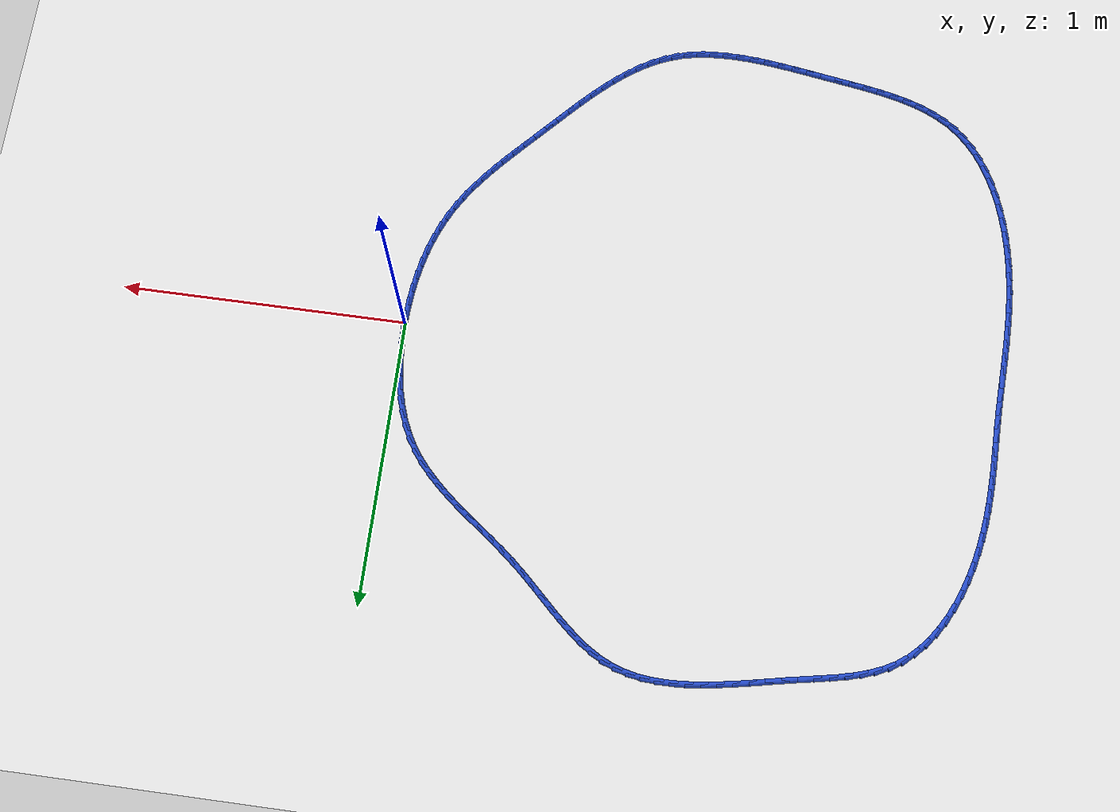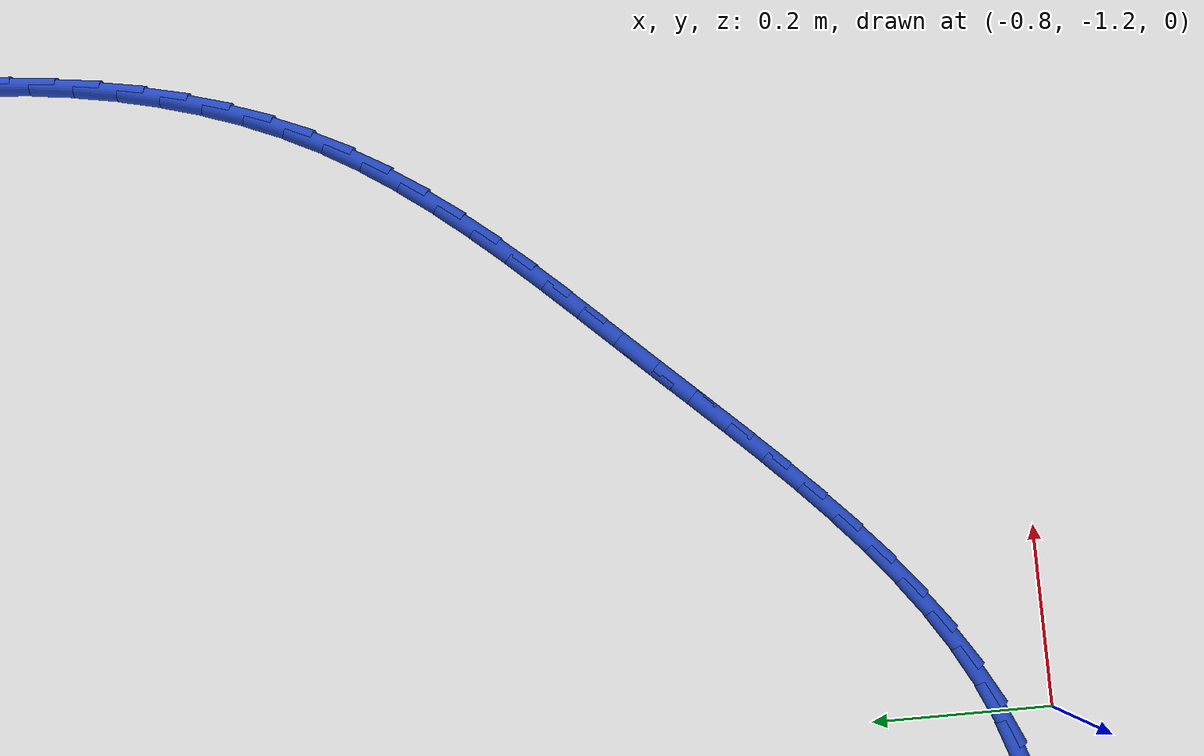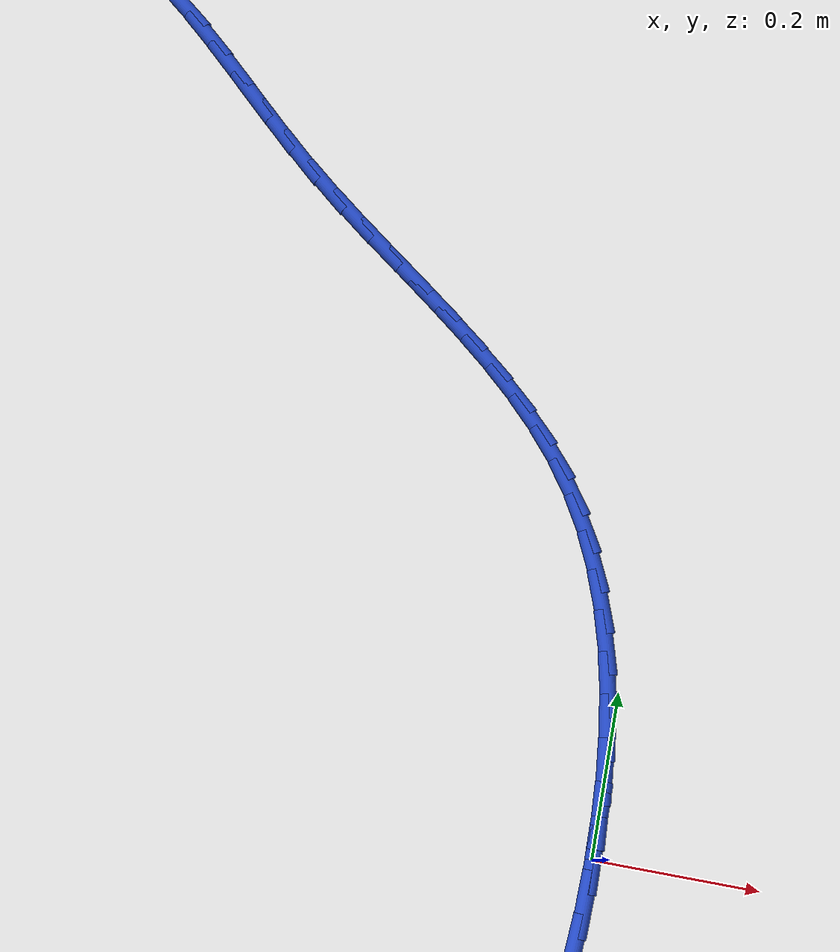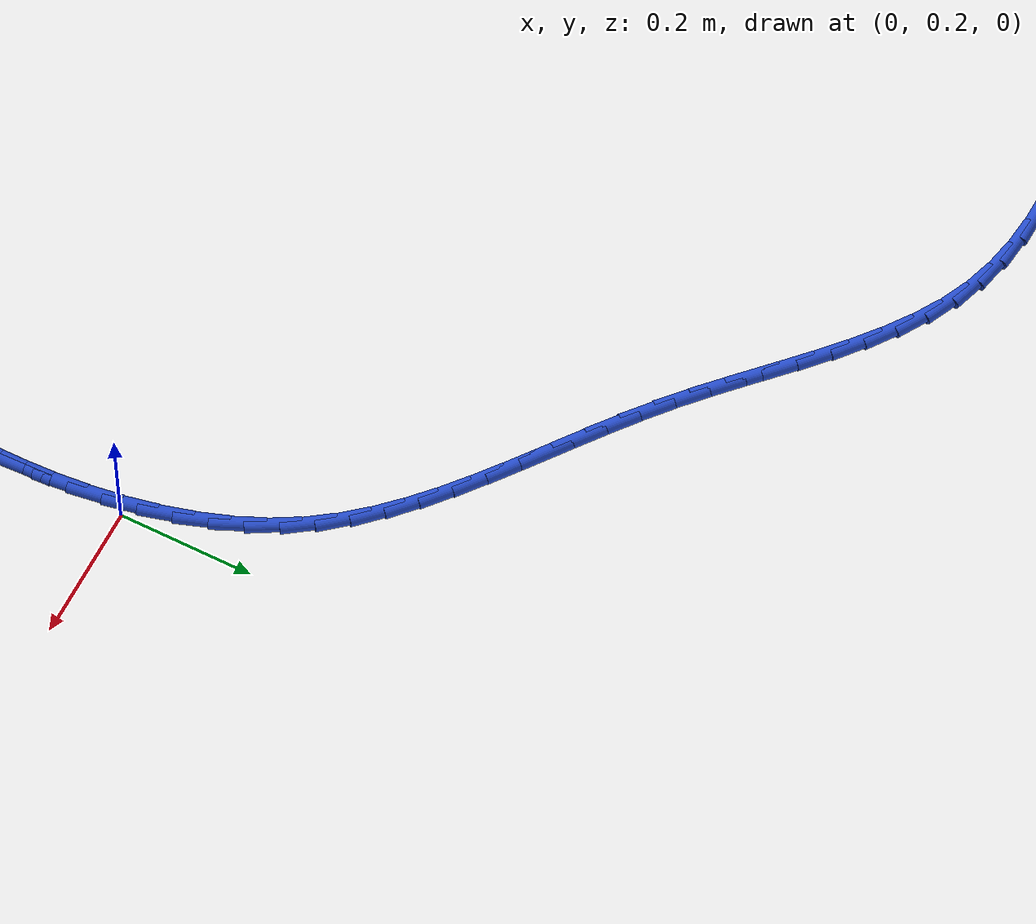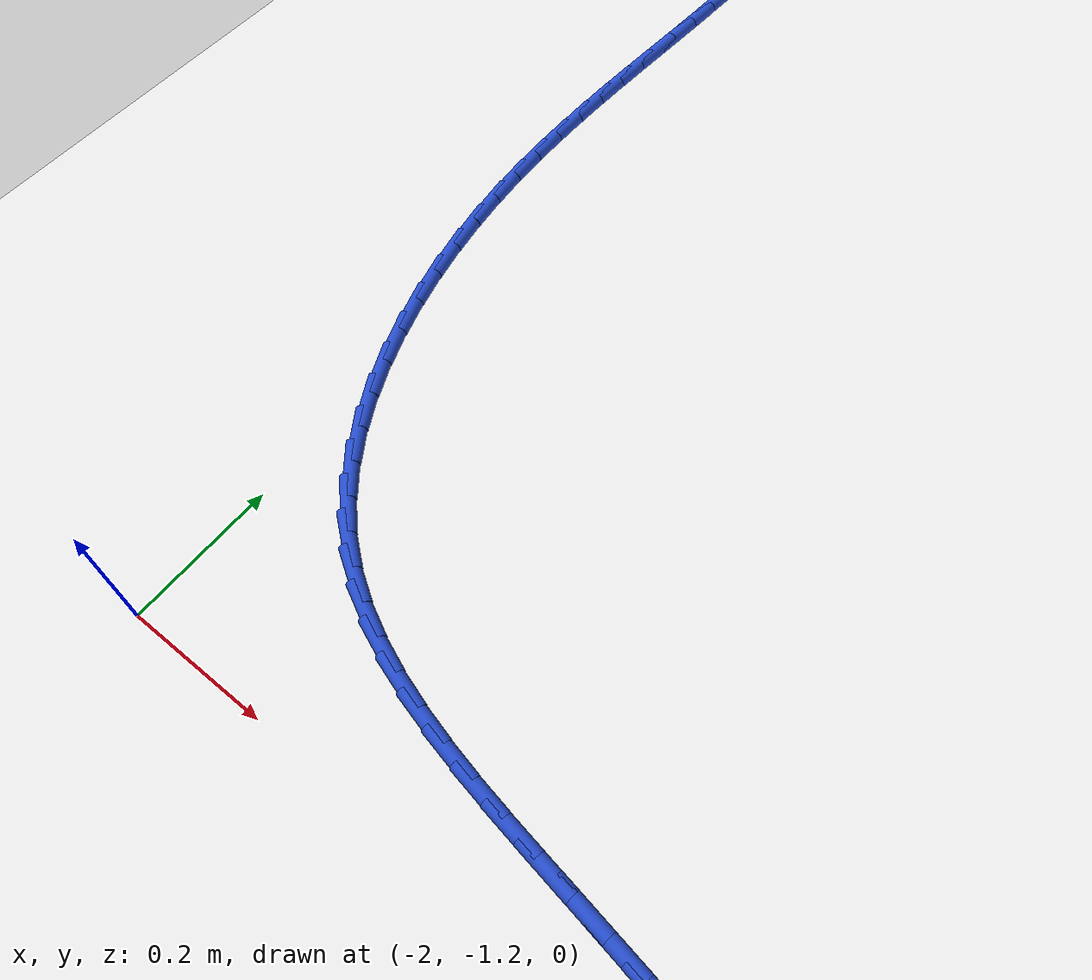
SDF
<sdf version="1.6">
 <world name="default">
  <light name="sun" type="directional">
   <pose>0 0 10 0 -0 0</pose>
   <diffuse>0.8 0.8 0.8 1</diffuse>
   <specular>0.2 0.2 0.2 1</specular>
   <attenuation>
    <range>1000</range>
    <constant>0.9</constant>
    <linear>0.01</linear>
    <quadratic>0.001</quadratic>
   </attenuation>
   <direction>-0.5 0.1 -0.9</direction>
  </light>
  <model name="ground_plane">
   <static>1</static>
   <link name="link">
    <collision name="collision">
     <geometry><plane><normal>0 0 1</normal><size>100 100</size></plane></geometry>
     <surface><friction><ode><mu>100</mu><mu2>50</mu2></ode></friction></surface>
    </collision>
    <visual name="visual">
     <cast_shadows>0</cast_shadows>
     <geometry><plane><normal>0 0 1</normal><size>100 100</size></plane></geometry>
     <material>
      <script><uri>file://media/materials/scripts/gazebo.material</uri><name>Gazebo/WhiteGlow</name></script>
     </material>
    </visual>
   </link>
  </model>
  <gravity>0 0 -9.8</gravity>
  <magnetic_field>6e-06 2.3e-05 -4.2e-05</magnetic_field>
  <atmosphere type="adiabatic"/>
  <physics name="default_physics" default="0" type="ode">
   <max_step_size>0.001</max_step_size>
   <real_time_factor>1</real_time_factor>
   <real_time_update_rate>1000</real_time_update_rate>
  </physics>
  <scene><ambient>0.4 0.4 0.4 1</ambient><background>0.7 0.7 0.7 1</background><shadows>1</shadows></scene>
  <spherical_coordinates>
   <surface_model>EARTH_WGS84</surface_model>
   <latitude_deg>0</latitude_deg>
   <longitude_deg>0</longitude_deg>
   <elevation>0</elevation>
   <heading_deg>0</heading_deg>
  </spherical_coordinates>
  <model name="line">
   <link name="link_0">
    <pose>4.683753385137379e-17 -1.3877787807814457e-17 0.01 0 1.57 -1.5644343418823194</pose>
    <collision name="collision">
     <geometry><cylinder><radius>0.01</radius><length>0.08</length></cylinder></geometry>
    </collision>
    <visual name="visual">
     <material>
      <script><name>Gazebo/Blue</name><uri>file://media/materials/scripts/gazebo.material</uri></script>
     </material>
     <geometry><cylinder><radius>0.01</radius><length>0.08</length></cylinder></geometry>
    </visual>
   </link>
   <link name="link_1">
    <pose>-0.0003307974758177523 0.051995252638659444 0.01 0 1.57 -1.5210663215368492</pose>
    <collision name="collision">
     <geometry><cylinder><radius>0.01</radius><length>0.08</length></cylinder></geometry>
    </collision>
    <visual name="visual">
     <material>
      <script><name>Gazebo/Blue</name><uri>file://media/materials/scripts/gazebo.material</uri></script>
     </material>
     <geometry><cylinder><radius>0.01</radius><length>0.08</length></cylinder></geometry>
    </visual>
   </link>
   <link name="link_2">
    <pose>-0.0029157111445098052 0.10393135057628536 0.01 0 1.57 -1.4733955420133573</pose>
    <collision name="collision">
     <geometry><cylinder><radius>0.01</radius><length>0.08</length></cylinder></geometry>
    </collision>
    <visual name="visual">
     <material>
      <script><name>Gazebo/Blue</name><uri>file://media/materials/scripts/gazebo.material</uri></script>
     </material>
     <geometry><cylinder><radius>0.01</radius><length>0.08</length></cylinder></geometry>
    </visual>
   </link>
   <link name="link_3">
    <pose>-0.007950227587354284 0.15545645587021534 0.01 0 1.57 -1.4206492175962093</pose>
    <collision name="collision">
     <geometry><cylinder><radius>0.01</radius><length>0.08</length></cylinder></geometry>
    </collision>
    <visual name="visual">
     <material>
      <script><name>Gazebo/Blue</name><uri>file://media/materials/scripts/gazebo.material</uri></script>
     </material>
     <geometry><cylinder><radius>0.01</radius><length>0.08</length></cylinder></geometry>
    </visual>
   </link>
   <link name="link_4">
    <pose>-0.01562983338562936 0.20621873057778703 0.01 0 1.57 -1.361987895294945</pose>
    <collision name="collision">
     <geometry><cylinder><radius>0.01</radius><length>0.08</length></cylinder></geometry>
    </collision>
    <visual name="visual">
     <material>
      <script><name>Gazebo/Blue</name><uri>file://media/materials/scripts/gazebo.material</uri></script>
     </material>
     <geometry><cylinder><radius>0.01</radius><length>0.08</length></cylinder></geometry>
    </visual>
   </link>
   <link name="link_5">
    <pose>-0.026150015120613216 0.25586633675633796 0.01 0 1.57 -1.296526748862627</pose>
    <collision name="collision">
     <geometry><cylinder><radius>0.01</radius><length>0.08</length></cylinder></geometry>
    </collision>
    <visual name="visual">
     <material>
      <script><name>Gazebo/Blue</name><uri>file://media/materials/scripts/gazebo.material</uri></script>
     </material>
     <geometry><cylinder><radius>0.01</radius><length>0.08</length></cylinder></geometry>
    </visual>
   </link>
   <link name="link_6">
    <pose>-0.03970625937358403 0.30404743646320576 0.01 0 1.57 -1.2233859840469603</pose>
    <collision name="collision">
     <geometry><cylinder><radius>0.01</radius><length>0.08</length></cylinder></geometry>
    </collision>
    <visual name="visual">
     <material>
      <script><name>Gazebo/Blue</name><uri>file://media/materials/scripts/gazebo.material</uri></script>
     </material>
     <geometry><cylinder><radius>0.01</radius><length>0.08</length></cylinder></geometry>
    </visual>
   </link>
   <link name="link_7">
    <pose>-0.056494052725819935 0.3504101917557281 0.01 0 1.57 -1.141784177607053</pose>
    <collision name="collision">
     <geometry><cylinder><radius>0.01</radius><length>0.08</length></cylinder></geometry>
    </collision>
    <visual name="visual">
     <material>
      <script><name>Gazebo/Blue</name><uri>file://media/materials/scripts/gazebo.material</uri></script>
     </material>
     <geometry><cylinder><radius>0.01</radius><length>0.08</length></cylinder></geometry>
    </visual>
   </link>
   <link name="link_8">
    <pose>-0.07670888175859918 0.3946027646912424 0.01 0 1.57 -1.0511877769248263</pose>
    <collision name="collision">
     <geometry><cylinder><radius>0.01</radius><length>0.08</length></cylinder></geometry>
    </collision>
    <visual name="visual">
     <material>
      <script><name>Gazebo/Blue</name><uri>file://media/materials/scripts/gazebo.material</uri></script>
     </material>
     <geometry><cylinder><radius>0.01</radius><length>0.08</length></cylinder></geometry>
    </visual>
   </link>
   <link name="link_9">
    <pose>-0.10054621030954501 0.43627334399175166 0.01 0 1.57 -0.955598606079556</pose>
    <collision name="collision">
     <geometry><cylinder><radius>0.01</radius><length>0.08</length></cylinder></geometry>
    </collision>
    <visual name="visual">
     <material>
      <script><name>Gazebo/Blue</name><uri>file://media/materials/scripts/gazebo.material</uri></script>
     </material>
     <geometry><cylinder><radius>0.01</radius><length>0.08</length></cylinder></geometry>
    </visual>
   </link>
   <link name="link_10">
    <pose>-0.12807121258728746 0.47522286996483815 0.01 0 1.57 -0.869791252039072</pose>
    <collision name="collision">
     <geometry><cylinder><radius>0.01</radius><length>0.08</length></cylinder></geometry>
    </collision>
    <visual name="visual">
     <material>
      <script><name>Gazebo/Blue</name><uri>file://media/materials/scripts/gazebo.material</uri></script>
     </material>
     <geometry><cylinder><radius>0.01</radius><length>0.08</length></cylinder></geometry>
    </visual>
   </link>
   <link name="link_11">
    <pose>-0.15891240422252556 0.5117642215171214 0.01 0 1.57 -0.797979003728878</pose>
    <collision name="collision">
     <geometry><cylinder><radius>0.01</radius><length>0.08</length></cylinder></geometry>
    </collision>
    <visual name="visual">
     <material>
      <script><name>Gazebo/Blue</name><uri>file://media/materials/scripts/gazebo.material</uri></script>
     </material>
     <geometry><cylinder><radius>0.01</radius><length>0.08</length></cylinder></geometry>
    </visual>
   </link>
   <link name="link_12">
    <pose>-0.19260692754647304 0.5463174036287529 0.01 0 1.57 -0.7405465630877671</pose>
    <collision name="collision">
     <geometry><cylinder><radius>0.01</radius><length>0.08</length></cylinder></geometry>
    </collision>
    <visual name="visual">
     <material>
      <script><name>Gazebo/Blue</name><uri>file://media/materials/scripts/gazebo.material</uri></script>
     </material>
     <geometry><cylinder><radius>0.01</radius><length>0.08</length></cylinder></geometry>
    </visual>
   </link>
   <link name="link_13">
    <pose>-0.22869192489034354 0.5793024212798845 0.01 0 1.57 -0.6972122695389328</pose>
    <collision name="collision">
     <geometry><cylinder><radius>0.01</radius><length>0.08</length></cylinder></geometry>
    </collision>
    <visual name="visual">
     <material>
      <script><name>Gazebo/Blue</name><uri>file://media/materials/scripts/gazebo.material</uri></script>
     </material>
     <geometry><cylinder><radius>0.01</radius><length>0.08</length></cylinder></geometry>
    </visual>
   </link>
   <link name="link_14">
    <pose>-0.2667045385853505 0.6111392794506676 0.01 0 1.57 -0.6673892667338394</pose>
    <collision name="collision">
     <geometry><cylinder><radius>0.01</radius><length>0.08</length></cylinder></geometry>
    </collision>
    <visual name="visual">
     <material>
      <script><name>Gazebo/Blue</name><uri>file://media/materials/scripts/gazebo.material</uri></script>
     </material>
     <geometry><cylinder><radius>0.01</radius><length>0.08</length></cylinder></geometry>
    </visual>
   </link>
   <link name="link_15">
    <pose>-0.3061819109627077 0.6422479831212539 0.01 0 1.57 -0.6504387336455774</pose>
    <collision name="collision">
     <geometry><cylinder><radius>0.01</radius><length>0.08</length></cylinder></geometry>
    </collision>
    <visual name="visual">
     <material>
      <script><name>Gazebo/Blue</name><uri>file://media/materials/scripts/gazebo.material</uri></script>
     </material>
     <geometry><cylinder><radius>0.01</radius><length>0.08</length></cylinder></geometry>
    </visual>
   </link>
   <link name="link_16">
    <pose>-0.34666118435362886 0.6730485372717954 0.01 0 1.57 -0.6458167741664425</pose>
    <collision name="collision">
     <geometry><cylinder><radius>0.01</radius><length>0.08</length></cylinder></geometry>
    </collision>
    <visual name="visual">
     <material>
      <script><name>Gazebo/Blue</name><uri>file://media/materials/scripts/gazebo.material</uri></script>
     </material>
     <geometry><cylinder><radius>0.01</radius><length>0.08</length></cylinder></geometry>
    </visual>
   </link>
   <link name="link_17">
    <pose>-0.3876795010893276 0.7039609468824435 0.01 0 1.57 -0.653139266784822</pose>
    <collision name="collision">
     <geometry><cylinder><radius>0.01</radius><length>0.08</length></cylinder></geometry>
    </collision>
    <visual name="visual">
     <material>
      <script><name>Gazebo/Blue</name><uri>file://media/materials/scripts/gazebo.material</uri></script>
     </material>
     <geometry><cylinder><radius>0.01</radius><length>0.08</length></cylinder></geometry>
    </visual>
   </link>
   <link name="link_18">
    <pose>-0.42877400350101724 0.7354052169333497 0.01 0 1.57 -0.6721874088499609</pose>
    <collision name="collision">
     <geometry><cylinder><radius>0.01</radius><length>0.08</length></cylinder></geometry>
    </collision>
    <visual name="visual">
     <material>
      <script><name>Gazebo/Blue</name><uri>file://media/materials/scripts/gazebo.material</uri></script>
     </material>
     <geometry><cylinder><radius>0.01</radius><length>0.08</length></cylinder></geometry>
    </visual>
   </link>
   <link name="link_19">
    <pose>-0.46948183391991194 0.7678013524046661 0.01 0 1.57 -0.7028391279737167</pose>
    <collision name="collision">
     <geometry><cylinder><radius>0.01</radius><length>0.08</length></cylinder></geometry>
    </collision>
    <visual name="visual">
     <material>
      <script><name>Gazebo/Blue</name><uri>file://media/materials/scripts/gazebo.material</uri></script>
     </material>
     <geometry><cylinder><radius>0.01</radius><length>0.08</length></cylinder></geometry>
    </visual>
   </link>
   <link name="link_20">
    <pose>-0.5093409532310753 0.8015681398144089 0.01 0 1.57 -0.7376154220492279</pose>
    <collision name="collision">
     <geometry><cylinder><radius>0.01</radius><length>0.08</length></cylinder></geometry>
    </collision>
    <visual name="visual">
     <material>
      <script><name>Gazebo/Blue</name><uri>file://media/materials/scripts/gazebo.material</uri></script>
     </material>
     <geometry><cylinder><radius>0.01</radius><length>0.08</length></cylinder></geometry>
    </visual>
   </link>
   <link name="link_21">
    <pose>-0.5481088657281727 0.8367975633201606 0.01 0 1.57 -0.759300013547368</pose>
    <collision name="collision">
     <geometry><cylinder><radius>0.01</radius><length>0.08</length></cylinder></geometry>
    </collision>
    <visual name="visual">
     <material>
      <script><name>Gazebo/Blue</name><uri>file://media/materials/scripts/gazebo.material</uri></script>
     </material>
     <geometry><cylinder><radius>0.01</radius><length>0.08</length></cylinder></geometry>
    </visual>
   </link>
   <link name="link_22">
    <pose>-0.5860576995810111 0.8728155613187568 0.01 0 1.57 -0.7656365040392238</pose>
    <collision name="collision">
     <geometry><cylinder><radius>0.01</radius><length>0.08</length></cylinder></geometry>
    </collision>
    <visual name="visual">
     <material>
      <script><name>Gazebo/Blue</name><uri>file://media/materials/scripts/gazebo.material</uri></script>
     </material>
     <geometry><cylinder><radius>0.01</radius><length>0.08</length></cylinder></geometry>
    </visual>
   </link>
   <link name="link_23">
    <pose>-0.6235332270140936 0.9088384490074132 0.01 0 1.57 -0.7564237669070555</pose>
    <collision name="collision">
     <geometry><cylinder><radius>0.01</radius><length>0.08</length></cylinder></geometry>
    </collision>
    <visual name="visual">
     <material>
      <script><name>Gazebo/Blue</name><uri>file://media/materials/scripts/gazebo.material</uri></script>
     </material>
     <geometry><cylinder><radius>0.01</radius><length>0.08</length></cylinder></geometry>
    </visual>
   </link>
   <link name="link_24">
    <pose>-0.6608812202519232 0.9440825415833445 0.01 0 1.57 -0.7309294811820358</pose>
    <collision name="collision">
     <geometry><cylinder><radius>0.01</radius><length>0.08</length></cylinder></geometry>
    </collision>
    <visual name="visual">
     <material>
      <script><name>Gazebo/Blue</name><uri>file://media/materials/scripts/gazebo.material</uri></script>
     </material>
     <geometry><cylinder><radius>0.01</radius><length>0.08</length></cylinder></geometry>
    </visual>
   </link>
   <link name="link_25">
    <pose>-0.6984474515190027 0.9777641542437658 0.01 0 1.57 -0.6878932398313794</pose>
    <collision name="collision">
     <geometry><cylinder><radius>0.01</radius><length>0.08</length></cylinder></geometry>
    </collision>
    <visual name="visual">
     <material>
      <script><name>Gazebo/Blue</name><uri>file://media/materials/scripts/gazebo.material</uri></script>
     </material>
     <geometry><cylinder><radius>0.01</radius><length>0.08</length></cylinder></geometry>
    </visual>
   </link>
   <link name="link_26">
    <pose>-0.7365776930398352 1.0090996021858925 0.01 0 1.57 -0.6256537897572199</pose>
    <collision name="collision">
     <geometry><cylinder><radius>0.01</radius><length>0.08</length></cylinder></geometry>
    </collision>
    <visual name="visual">
     <material>
      <script><name>Gazebo/Blue</name><uri>file://media/materials/scripts/gazebo.material</uri></script>
     </material>
     <geometry><cylinder><radius>0.01</radius><length>0.08</length></cylinder></geometry>
    </visual>
   </link>
   <link name="link_27">
    <pose>-0.7756177170389236 1.037305200606939 0.01 0 1.57 -0.542510169133785</pose>
    <collision name="collision">
     <geometry><cylinder><radius>0.01</radius><length>0.08</length></cylinder></geometry>
    </collision>
    <visual name="visual">
     <material>
      <script><name>Gazebo/Blue</name><uri>file://media/materials/scripts/gazebo.material</uri></script>
     </material>
     <geometry><cylinder><radius>0.01</radius><length>0.08</length></cylinder></geometry>
    </visual>
   </link>
   <link name="link_28">
    <pose>-0.8159132957407711 1.0615972647041212 0.01 0 1.57 -0.4374800167780543</pose>
    <collision name="collision">
     <geometry><cylinder><radius>0.01</radius><length>0.08</length></cylinder></geometry>
    </collision>
    <visual name="visual">
     <material>
      <script><name>Gazebo/Blue</name><uri>file://media/materials/scripts/gazebo.material</uri></script>
     </material>
     <geometry><cylinder><radius>0.01</radius><length>0.08</length></cylinder></geometry>
    </visual>
   </link>
   <link name="link_29">
    <pose>-0.8578100038909581 1.0811925926896728 0.01 0 1.57 -0.31869657315777666</pose>
    <collision name="collision">
     <geometry><cylinder><radius>0.01</radius><length>0.08</length></cylinder></geometry>
    </collision>
    <visual name="visual">
     <material>
      <script><name>Gazebo/Blue</name><uri>file://media/materials/scripts/gazebo.material</uri></script>
     </material>
     <geometry><cylinder><radius>0.01</radius><length>0.08</length></cylinder></geometry>
    </visual>
   </link>
   <link name="link_30">
    <pose>-0.9015271640555624 1.0956167838271447 0.01 0 1.57 -0.20868096727724847</pose>
    <collision name="collision">
     <geometry><cylinder><radius>0.01</radius><length>0.08</length></cylinder></geometry>
    </collision>
    <visual name="visual">
     <material>
      <script><name>Gazebo/Blue</name><uri>file://media/materials/scripts/gazebo.material</uri></script>
     </material>
     <geometry><cylinder><radius>0.01</radius><length>0.08</length></cylinder></geometry>
    </visual>
   </link>
   <link name="link_31">
    <pose>-0.9469413128006703 1.105233859952997 0.01 0 1.57 -0.11277137897586513</pose>
    <collision name="collision">
     <geometry><cylinder><radius>0.01</radius><length>0.08</length></cylinder></geometry>
    </collision>
    <visual name="visual">
     <material>
      <script><name>Gazebo/Blue</name><uri>file://media/materials/scripts/gazebo.material</uri></script>
     </material>
     <geometry><cylinder><radius>0.01</radius><length>0.08</length></cylinder></geometry>
    </visual>
   </link>
   <link name="link_32">
    <pose>-0.9938713664832474 1.110548776559041 0.01 0 1.57 -0.03143513016036987</pose>
    <collision name="collision">
     <geometry><cylinder><radius>0.01</radius><length>0.08</length></cylinder></geometry>
    </collision>
    <visual name="visual">
     <material>
      <script><name>Gazebo/Blue</name><uri>file://media/materials/scripts/gazebo.material</uri></script>
     </material>
     <geometry><cylinder><radius>0.01</radius><length>0.08</length></cylinder></geometry>
    </visual>
   </link>
   <link name="link_33">
    <pose>-1.0421362414602608 1.1120664891370888 0.01 0 1.57 0.03589282977141568</pose>
    <collision name="collision">
     <geometry><cylinder><radius>0.01</radius><length>0.08</length></cylinder></geometry>
    </collision>
    <visual name="visual">
     <material>
      <script><name>Gazebo/Blue</name><uri>file://media/materials/scripts/gazebo.material</uri></script>
     </material>
     <geometry><cylinder><radius>0.01</radius><length>0.08</length></cylinder></geometry>
    </visual>
   </link>
   <link name="link_34">
    <pose>-1.0915548540886764 1.110291953178951 0.01 0 1.57 0.09028207268165225</pose>
    <collision name="collision">
     <geometry><cylinder><radius>0.01</radius><length>0.08</length></cylinder></geometry>
    </collision>
    <visual name="visual">
     <material>
      <script><name>Gazebo/Blue</name><uri>file://media/materials/scripts/gazebo.material</uri></script>
     </material>
     <geometry><cylinder><radius>0.01</radius><length>0.08</length></cylinder></geometry>
    </visual>
   </link>
   <link name="link_35">
    <pose>-1.1419461207254604 1.1057301241764395 0.01 0 1.57 0.13293137946179848</pose>
    <collision name="collision">
     <geometry><cylinder><radius>0.01</radius><length>0.08</length></cylinder></geometry>
    </collision>
    <visual name="visual">
     <material>
      <script><name>Gazebo/Blue</name><uri>file://media/materials/scripts/gazebo.material</uri></script>
     </material>
     <geometry><cylinder><radius>0.01</radius><length>0.08</length></cylinder></geometry>
    </visual>
   </link>
   <link name="link_36">
    <pose>-1.1931289577275788 1.0988859576213652 0.01 0 1.57 0.16494818981463039</pose>
    <collision name="collision">
     <geometry><cylinder><radius>0.01</radius><length>0.08</length></cylinder></geometry>
    </collision>
    <visual name="visual">
     <material>
      <script><name>Gazebo/Blue</name><uri>file://media/materials/scripts/gazebo.material</uri></script>
     </material>
     <geometry><cylinder><radius>0.01</radius><length>0.08</length></cylinder></geometry>
    </visual>
   </link>
   <link name="link_37">
    <pose>-1.2449222814519982 1.0902644090055393 0.01 0 1.57 0.18723807308191537</pose>
    <collision name="collision">
     <geometry><cylinder><radius>0.01</radius><length>0.08</length></cylinder></geometry>
    </collision>
    <visual name="visual">
     <material>
      <script><name>Gazebo/Blue</name><uri>file://media/materials/scripts/gazebo.material</uri></script>
     </material>
     <geometry><cylinder><radius>0.01</radius><length>0.08</length></cylinder></geometry>
    </visual>
   </link>
   <link name="link_38">
    <pose>-1.2971450082556841 1.0803704338207734 0.01 0 1.57 0.20045831214298673</pose>
    <collision name="collision">
     <geometry><cylinder><radius>0.01</radius><length>0.08</length></cylinder></geometry>
    </collision>
    <visual name="visual">
     <material>
      <script><name>Gazebo/Blue</name><uri>file://media/materials/scripts/gazebo.material</uri></script>
     </material>
     <geometry><cylinder><radius>0.01</radius><length>0.08</length></cylinder></geometry>
    </visual>
   </link>
   <link name="link_39">
    <pose>-1.349616054495604 1.0697089875588792 0.01 0 1.57 0.20500290673838595</pose>
    <collision name="collision">
     <geometry><cylinder><radius>0.01</radius><length>0.08</length></cylinder></geometry>
    </collision>
    <visual name="visual">
     <material>
      <script><name>Gazebo/Blue</name><uri>file://media/materials/scripts/gazebo.material</uri></script>
     </material>
     <geometry><cylinder><radius>0.01</radius><length>0.08</length></cylinder></geometry>
    </visual>
   </link>
   <link name="link_40">
    <pose>-1.402154336528723 1.058785025711667 0.01 0 1.57 0.20099951129701538</pose>
    <collision name="collision">
     <geometry><cylinder><radius>0.01</radius><length>0.08</length></cylinder></geometry>
    </collision>
    <visual name="visual">
     <material>
      <script><name>Gazebo/Blue</name><uri>file://media/materials/scripts/gazebo.material</uri></script>
     </material>
     <geometry><cylinder><radius>0.01</radius><length>0.08</length></cylinder></geometry>
    </visual>
   </link>
   <link name="link_41">
    <pose>-1.4545787707120077 1.0481035037709487 0.01 0 1.57 0.19035575516878378</pose>
    <collision name="collision">
     <geometry><cylinder><radius>0.01</radius><length>0.08</length></cylinder></geometry>
    </collision>
    <visual name="visual">
     <material>
      <script><name>Gazebo/Blue</name><uri>file://media/materials/scripts/gazebo.material</uri></script>
     </material>
     <geometry><cylinder><radius>0.01</radius><length>0.08</length></cylinder></geometry>
    </visual>
   </link>
   <link name="link_42">
    <pose>-1.5066891190608542 1.0380624245166032 0.01 0 1.57 0.18979165449557356</pose>
    <collision name="collision">
     <geometry><cylinder><radius>0.01</radius><length>0.08</length></cylinder></geometry>
    </collision>
    <visual name="visual">
     <material>
      <script><name>Gazebo/Blue</name><uri>file://media/materials/scripts/gazebo.material</uri></script>
     </material>
     <geometry><cylinder><radius>0.01</radius><length>0.08</length></cylinder></geometry>
    </visual>
   </link>
   <link name="link_43">
    <pose>-1.5581277363635657 1.0281808709414084 0.01 0 1.57 0.20822228529177902</pose>
    <collision name="collision">
     <geometry><cylinder><radius>0.01</radius><length>0.08</length></cylinder></geometry>
    </collision>
    <visual name="visual">
     <material>
      <script><name>Gazebo/Blue</name><uri>file://media/materials/scripts/gazebo.material</uri></script>
     </material>
     <geometry><cylinder><radius>0.01</radius><length>0.08</length></cylinder></geometry>
    </visual>
   </link>
   <link name="link_44">
    <pose>-1.608459711888231 1.0175464960724767 0.01 0 1.57 0.24700412809022887</pose>
    <collision name="collision">
     <geometry><cylinder><radius>0.01</radius><length>0.08</length></cylinder></geometry>
    </collision>
    <visual name="visual">
     <material>
      <script><name>Gazebo/Blue</name><uri>file://media/materials/scripts/gazebo.material</uri></script>
     </material>
     <geometry><cylinder><radius>0.01</radius><length>0.08</length></cylinder></geometry>
    </visual>
   </link>
   <link name="link_45">
    <pose>-1.657249601015596 1.0052439718530408 0.01 0 1.57 0.3078813010276879</pose>
    <collision name="collision">
     <geometry><cylinder><radius>0.01</radius><length>0.08</length></cylinder></geometry>
    </collision>
    <visual name="visual">
     <material>
      <script><name>Gazebo/Blue</name><uri>file://media/materials/scripts/gazebo.material</uri></script>
     </material>
     <geometry><cylinder><radius>0.01</radius><length>0.08</length></cylinder></geometry>
    </visual>
   </link>
   <link name="link_46">
    <pose>-1.7040619591264083 0.9903579702263322 0.01 0 1.57 0.3925833586291731</pose>
    <collision name="collision">
     <geometry><cylinder><radius>0.01</radius><length>0.08</length></cylinder></geometry>
    </collision>
    <visual name="visual">
     <material>
      <script><name>Gazebo/Blue</name><uri>file://media/materials/scripts/gazebo.material</uri></script>
     </material>
     <geometry><cylinder><radius>0.01</radius><length>0.08</length></cylinder></geometry>
    </visual>
   </link>
   <link name="link_47">
    <pose>-1.7484613416014139 0.9719731631355837 0.01 0 1.57 0.5018432439867829</pose>
    <collision name="collision">
     <geometry><cylinder><radius>0.01</radius><length>0.08</length></cylinder></geometry>
    </collision>
    <visual name="visual">
     <material>
      <script><name>Gazebo/Blue</name><uri>file://media/materials/scripts/gazebo.material</uri></script>
     </material>
     <geometry><cylinder><radius>0.01</radius><length>0.08</length></cylinder></geometry>
    </visual>
   </link>
   <link name="link_48">
    <pose>-1.7900123038213607 0.9491742225240279 0.01 0 1.57 0.6302608758906472</pose>
    <collision name="collision">
     <geometry><cylinder><radius>0.01</radius><length>0.08</length></cylinder></geometry>
    </collision>
    <visual name="visual">
     <material>
      <script><name>Gazebo/Blue</name><uri>file://media/materials/scripts/gazebo.material</uri></script>
     </material>
     <geometry><cylinder><radius>0.01</radius><length>0.08</length></cylinder></geometry>
    </visual>
   </link>
   <link name="link_49">
    <pose>-1.828338109807432 0.921214996509267 0.01 0 1.57 0.7533784462173198</pose>
    <collision name="collision">
     <geometry><cylinder><radius>0.01</radius><length>0.08</length></cylinder></geometry>
    </collision>
    <visual name="visual">
     <material>
      <script><name>Gazebo/Blue</name><uri>file://media/materials/scripts/gazebo.material</uri></script>
     </material>
     <geometry><cylinder><radius>0.01</radius><length>0.08</length></cylinder></geometry>
    </visual>
   </link>
   <link name="link_50">
    <pose>-1.8634016368961643 0.8883279707830062 0.01 0 1.57 0.8625811211916941</pose>
    <collision name="collision">
     <geometry><cylinder><radius>0.01</radius><length>0.08</length></cylinder></geometry>
    </collision>
    <visual name="visual">
     <material>
      <script><name>Gazebo/Blue</name><uri>file://media/materials/scripts/gazebo.material</uri></script>
     </material>
     <geometry><cylinder><radius>0.01</radius><length>0.08</length></cylinder></geometry>
    </visual>
   </link>
   <link name="link_51">
    <pose>-1.8952875992482943 0.8510967188438283 0.01 0 1.57 0.9584471731648041</pose>
    <collision name="collision">
     <geometry><cylinder><radius>0.01</radius><length>0.08</length></cylinder></geometry>
    </collision>
    <visual name="visual">
     <material>
      <script><name>Gazebo/Blue</name><uri>file://media/materials/scripts/gazebo.material</uri></script>
     </material>
     <geometry><cylinder><radius>0.01</radius><length>0.08</length></cylinder></geometry>
    </visual>
   </link>
   <link name="link_52">
    <pose>-1.9240808682261983 0.8101052671861909 0.01 0 1.57 1.0423672182753734</pose>
    <collision name="collision">
     <geometry><cylinder><radius>0.01</radius><length>0.08</length></cylinder></geometry>
    </collision>
    <visual name="visual">
     <material>
      <script><name>Gazebo/Blue</name><uri>file://media/materials/scripts/gazebo.material</uri></script>
     </material>
     <geometry><cylinder><radius>0.01</radius><length>0.08</length></cylinder></geometry>
    </visual>
   </link>
   <link name="link_53">
    <pose>-1.9498663151922533 0.7659376423045526 0.01 0 1.57 1.1160397091845151</pose>
    <collision name="collision">
     <geometry><cylinder><radius>0.01</radius><length>0.08</length></cylinder></geometry>
    </collision>
    <visual name="visual">
     <material>
      <script><name>Gazebo/Blue</name><uri>file://media/materials/scripts/gazebo.material</uri></script>
     </material>
     <geometry><cylinder><radius>0.01</radius><length>0.08</length></cylinder></geometry>
    </visual>
   </link>
   <link name="link_54">
    <pose>-1.9727288115088355 0.7191778706933715 0.01 0 1.57 1.1811799230710796</pose>
    <collision name="collision">
     <geometry><cylinder><radius>0.01</radius><length>0.08</length></cylinder></geometry>
    </collision>
    <visual name="visual">
     <material>
      <script><name>Gazebo/Blue</name><uri>file://media/materials/scripts/gazebo.material</uri></script>
     </material>
     <geometry><cylinder><radius>0.01</radius><length>0.08</length></cylinder></geometry>
    </visual>
   </link>
   <link name="link_55">
    <pose>-1.9927532285383216 0.6704099788471052 0.01 0 1.57 1.2393846544069853</pose>
    <collision name="collision">
     <geometry><cylinder><radius>0.01</radius><length>0.08</length></cylinder></geometry>
    </collision>
    <visual name="visual">
     <material>
      <script><name>Gazebo/Blue</name><uri>file://media/materials/scripts/gazebo.material</uri></script>
     </material>
     <geometry><cylinder><radius>0.01</radius><length>0.08</length></cylinder></geometry>
    </visual>
   </link>
   <link name="link_56">
    <pose>-2.010024437643088 0.6202179932602125 0.01 0 1.57 1.2920929670523353</pose>
    <collision name="collision">
     <geometry><cylinder><radius>0.01</radius><length>0.08</length></cylinder></geometry>
    </collision>
    <visual name="visual">
     <material>
      <script><name>Gazebo/Blue</name><uri>file://media/materials/scripts/gazebo.material</uri></script>
     </material>
     <geometry><cylinder><radius>0.01</radius><length>0.08</length></cylinder></geometry>
    </visual>
   </link>
   <link name="link_57">
    <pose>-2.0246273101855112 0.569185940427151 0.01 0 1.57 1.3405996503066306</pose>
    <collision name="collision">
     <geometry><cylinder><radius>0.01</radius><length>0.08</length></cylinder></geometry>
    </collision>
    <visual name="visual">
     <material>
      <script><name>Gazebo/Blue</name><uri>file://media/materials/scripts/gazebo.material</uri></script>
     </material>
     <geometry><cylinder><radius>0.01</radius><length>0.08</length></cylinder></geometry>
    </visual>
   </link>
   <link name="link_58">
    <pose>-2.0366467175279683 0.5178978468423796 0.01 0 1.57 1.385920003829943</pose>
    <collision name="collision">
     <geometry><cylinder><radius>0.01</radius><length>0.08</length></cylinder></geometry>
    </collision>
    <visual name="visual">
     <material>
      <script><name>Gazebo/Blue</name><uri>file://media/materials/scripts/gazebo.material</uri></script>
     </material>
     <geometry><cylinder><radius>0.01</radius><length>0.08</length></cylinder></geometry>
    </visual>
   </link>
   <link name="link_59">
    <pose>-2.046184398417875 0.46689743359977226 0.01 0 1.57 1.4270324355167208</pose>
    <collision name="collision">
     <geometry><cylinder><radius>0.01</radius><length>0.08</length></cylinder></geometry>
    </collision>
    <visual name="visual">
     <material>
      <script><name>Gazebo/Blue</name><uri>file://media/materials/scripts/gazebo.material</uri></script>
     </material>
     <geometry><cylinder><radius>0.01</radius><length>0.08</length></cylinder></geometry>
    </visual>
   </link>
   <link name="link_60">
    <pose>-2.0535024731172316 0.4163451827092194 0.01 0 1.57 1.4625729472241138</pose>
    <collision name="collision">
     <geometry><cylinder><radius>0.01</radius><length>0.08</length></cylinder></geometry>
    </collision>
    <visual name="visual">
     <material>
      <script><name>Gazebo/Blue</name><uri>file://media/materials/scripts/gazebo.material</uri></script>
     </material>
     <geometry><cylinder><radius>0.01</radius><length>0.08</length></cylinder></geometry>
    </visual>
   </link>
   <link name="link_61">
    <pose>-2.058951770782168 0.36618960215470947 0.01 0 1.57 1.4920181506602441</pose>
    <collision name="collision">
     <geometry><cylinder><radius>0.01</radius><length>0.08</length></cylinder></geometry>
    </collision>
    <visual name="visual">
     <material>
      <script><name>Gazebo/Blue</name><uri>file://media/materials/scripts/gazebo.material</uri></script>
     </material>
     <geometry><cylinder><radius>0.01</radius><length>0.08</length></cylinder></geometry>
    </visual>
   </link>
   <link name="link_62">
    <pose>-2.0628840578135423 0.3163769603303837 0.01 0 1.57 1.5149809582141855</pose>
    <collision name="collision">
     <geometry><cylinder><radius>0.01</radius><length>0.08</length></cylinder></geometry>
    </collision>
    <visual name="visual">
     <material>
      <script><name>Gazebo/Blue</name><uri>file://media/materials/scripts/gazebo.material</uri></script>
     </material>
     <geometry><cylinder><radius>0.01</radius><length>0.08</length></cylinder></geometry>
    </visual>
   </link>
   <link name="link_63">
    <pose>-2.065651100612216 0.2668535256303827 0.01 0 1.57 1.531181318369974</pose>
    <collision name="collision">
     <geometry><cylinder><radius>0.01</radius><length>0.08</length></cylinder></geometry>
    </collision>
    <visual name="visual">
     <material>
      <script><name>Gazebo/Blue</name><uri>file://media/materials/scripts/gazebo.material</uri></script>
     </material>
     <geometry><cylinder><radius>0.01</radius><length>0.08</length></cylinder></geometry>
    </visual>
   </link>
   <link name="link_64">
    <pose>-2.0676046655790468 0.21756556644884792 0.01 0 1.57 1.5404255313347133</pose>
    <collision name="collision">
     <geometry><cylinder><radius>0.01</radius><length>0.08</length></cylinder></geometry>
    </collision>
    <visual name="visual">
     <material>
      <script><name>Gazebo/Blue</name><uri>file://media/materials/scripts/gazebo.material</uri></script>
     </material>
     <geometry><cylinder><radius>0.01</radius><length>0.08</length></cylinder></geometry>
    </visual>
   </link>
   <link name="link_65">
    <pose>-2.069096519114894 0.16845935117992009 0.01 0 1.57 1.5425890448365747</pose>
    <collision name="collision">
     <geometry><cylinder><radius>0.01</radius><length>0.08</length></cylinder></geometry>
    </collision>
    <visual name="visual">
     <material>
      <script><name>Gazebo/Blue</name><uri>file://media/materials/scripts/gazebo.material</uri></script>
     </material>
     <geometry><cylinder><radius>0.01</radius><length>0.08</length></cylinder></geometry>
    </visual>
   </link>
   <link name="link_66">
    <pose>-2.0704784276206176 0.11948114821773959 0.01 0 1.57 1.5376060727659269</pose>
    <collision name="collision">
     <geometry><cylinder><radius>0.01</radius><length>0.08</length></cylinder></geometry>
    </collision>
    <visual name="visual">
     <material>
      <script><name>Gazebo/Blue</name><uri>file://media/materials/scripts/gazebo.material</uri></script>
     </material>
     <geometry><cylinder><radius>0.01</radius><length>0.08</length></cylinder></geometry>
    </visual>
   </link>
   <link name="link_67">
    <pose>-2.072102157497076 0.07057722595644829 0.01 0 1.57 1.5265348261270975</pose>
    <collision name="collision">
     <geometry><cylinder><radius>0.01</radius><length>0.08</length></cylinder></geometry>
    </collision>
    <visual name="visual">
     <material>
      <script><name>Gazebo/Blue</name><uri>file://media/materials/scripts/gazebo.material</uri></script>
     </material>
     <geometry><cylinder><radius>0.01</radius><length>0.08</length></cylinder></geometry>
    </visual>
   </link>
   <link name="link_68">
    <pose>-2.0742671745278836 0.021694946790480542 0.01 0 1.57 1.5171356032590597</pose>
    <collision name="collision">
     <geometry><cylinder><radius>0.01</radius><length>0.08</length></cylinder></geometry>
    </collision>
    <visual name="visual">
     <material>
      <script><name>Gazebo/Blue</name><uri>file://media/materials/scripts/gazebo.material</uri></script>
     </material>
     <geometry><cylinder><radius>0.01</radius><length>0.08</length></cylinder></geometry>
    </visual>
   </link>
   <link name="link_69">
    <pose>-2.076893992597407 -0.027210400143920472 0.01 0 1.57 1.512821156511768</pose>
    <collision name="collision">
     <geometry><cylinder><radius>0.01</radius><length>0.08</length></cylinder></geometry>
    </collision>
    <visual name="visual">
     <material>
      <script><name>Gazebo/Blue</name><uri>file://media/materials/scripts/gazebo.material</uri></script>
     </material>
     <geometry><cylinder><radius>0.01</radius><length>0.08</length></cylinder></geometry>
    </visual>
   </link>
   <link name="link_70">
    <pose>-2.079736200509778 -0.0761800340483395 0.01 0 1.57 1.5135902905626182</pose>
    <collision name="collision">
     <geometry><cylinder><radius>0.01</radius><length>0.08</length></cylinder></geometry>
    </collision>
    <visual name="visual">
     <material>
      <script><name>Gazebo/Blue</name><uri>file://media/materials/scripts/gazebo.material</uri></script>
     </material>
     <geometry><cylinder><radius>0.01</radius><length>0.08</length></cylinder></geometry>
    </visual>
   </link>
   <link name="link_71">
    <pose>-2.082546660322398 -0.12525515892260541 0.01 0 1.57 1.5194096632417813</pose>
    <collision name="collision">
     <geometry><cylinder><radius>0.01</radius><length>0.08</length></cylinder></geometry>
    </collision>
    <visual name="visual">
     <material>
      <script><name>Gazebo/Blue</name><uri>file://media/materials/scripts/gazebo.material</uri></script>
     </material>
     <geometry><cylinder><radius>0.01</radius><length>0.08</length></cylinder></geometry>
    </visual>
   </link>
   <link name="link_72">
    <pose>-2.085078234092666 -0.17447697876654816 0.01 0 1.57 1.5302284082251352</pose>
    <collision name="collision">
     <geometry><cylinder><radius>0.01</radius><length>0.08</length></cylinder></geometry>
    </collision>
    <visual name="visual">
     <material>
      <script><name>Gazebo/Blue</name><uri>file://media/materials/scripts/gazebo.material</uri></script>
     </material>
     <geometry><cylinder><radius>0.01</radius><length>0.08</length></cylinder></geometry>
    </visual>
   </link>
   <link name="link_73">
    <pose>-2.087083783877985 -0.2238866975799982 0.01 0 1.57 1.545974328633852</pose>
    <collision name="collision">
     <geometry><cylinder><radius>0.01</radius><length>0.08</length></cylinder></geometry>
    </collision>
    <visual name="visual">
     <material>
      <script><name>Gazebo/Blue</name><uri>file://media/materials/scripts/gazebo.material</uri></script>
     </material>
     <geometry><cylinder><radius>0.01</radius><length>0.08</length></cylinder></geometry>
    </visual>
   </link>
   <link name="link_74">
    <pose>-2.0883161717357552 -0.2735255193627836 0.01 0 1.57 1.566546869505128</pose>
    <collision name="collision">
     <geometry><cylinder><radius>0.01</radius><length>0.08</length></cylinder></geometry>
    </collision>
    <visual name="visual">
     <material>
      <script><name>Gazebo/Blue</name><uri>file://media/materials/scripts/gazebo.material</uri></script>
     </material>
     <geometry><cylinder><radius>0.01</radius><length>0.08</length></cylinder></geometry>
    </visual>
   </link>
   <link name="link_75">
    <pose>-2.088528259723378 -0.32343464811473477 0.01 0 1.57 -1.549785154398921</pose>
    <collision name="collision">
     <geometry><cylinder><radius>0.01</radius><length>0.08</length></cylinder></geometry>
    </collision>
    <visual name="visual">
     <material>
      <script><name>Gazebo/Blue</name><uri>file://media/materials/scripts/gazebo.material</uri></script>
     </material>
     <geometry><cylinder><radius>0.01</radius><length>0.08</length></cylinder></geometry>
    </visual>
   </link>
   <link name="link_76">
    <pose>-2.087472909898255 -0.37365528783568136 0.01 0 1.57 -1.520024196740073</pose>
    <collision name="collision">
     <geometry><cylinder><radius>0.01</radius><length>0.08</length></cylinder></geometry>
    </collision>
    <visual name="visual">
     <material>
      <script><name>Gazebo/Blue</name><uri>file://media/materials/scripts/gazebo.material</uri></script>
     </material>
     <geometry><cylinder><radius>0.01</radius><length>0.08</length></cylinder></geometry>
    </visual>
   </link>
   <link name="link_77">
    <pose>-2.084902984317786 -0.4242286425254529 0.01 0 1.57 -1.4860114306847125</pose>
    <collision name="collision">
     <geometry><cylinder><radius>0.01</radius><length>0.08</length></cylinder></geometry>
    </collision>
    <visual name="visual">
     <material>
      <script><name>Gazebo/Blue</name><uri>file://media/materials/scripts/gazebo.material</uri></script>
     </material>
     <geometry><cylinder><radius>0.01</radius><length>0.08</length></cylinder></geometry>
    </visual>
   </link>
   <link name="link_78">
    <pose>-2.080571345039374 -0.4751959161838799 0.01 0 1.57 -1.448066176140936</pose>
    <collision name="collision">
     <geometry><cylinder><radius>0.01</radius><length>0.08</length></cylinder></geometry>
    </collision>
    <visual name="visual">
     <material>
      <script><name>Gazebo/Blue</name><uri>file://media/materials/scripts/gazebo.material</uri></script>
     </material>
     <geometry><cylinder><radius>0.01</radius><length>0.08</length></cylinder></geometry>
    </visual>
   </link>
   <link name="link_79">
    <pose>-2.074230854268975 -0.5265983122058692 0.01 0 1.57 -1.4067299461371605</pose>
    <collision name="collision">
     <geometry><cylinder><radius>0.01</radius><length>0.08</length></cylinder></geometry>
    </collision>
    <visual name="visual">
     <material>
      <script><name>Gazebo/Blue</name><uri>file://media/materials/scripts/gazebo.material</uri></script>
     </material>
     <geometry><cylinder><radius>0.01</radius><length>0.08</length></cylinder></geometry>
    </visual>
   </link>
   <link name="link_80">
    <pose>-2.065658076801359 -0.5783805177142529 0.01 0 1.57 -1.362451264687425</pose>
    <collision name="collision">
     <geometry><cylinder><radius>0.01</radius><length>0.08</length></cylinder></geometry>
    </collision>
    <visual name="visual">
     <material>
      <script><name>Gazebo/Blue</name><uri>file://media/materials/scripts/gazebo.material</uri></script>
     </material>
     <geometry><cylinder><radius>0.01</radius><length>0.08</length></cylinder></geometry>
    </visual>
   </link>
   <link name="link_81">
    <pose>-2.0547191949970753 -0.6301222996355275 0.01 0 1.57 -1.3144723866468844</pose>
    <collision name="collision">
     <geometry><cylinder><radius>0.01</radius><length>0.08</length></cylinder></geometry>
    </collision>
    <visual name="visual">
     <material>
      <script><name>Gazebo/Blue</name><uri>file://media/materials/scripts/gazebo.material</uri></script>
     </material>
     <geometry><cylinder><radius>0.01</radius><length>0.08</length></cylinder></geometry>
    </visual>
   </link>
   <link name="link_82">
    <pose>-2.0413015677738326 -0.6813171945536404 0.01 0 1.57 -1.2617498716194702</pose>
    <collision name="collision">
     <geometry><cylinder><radius>0.01</radius><length>0.08</length></cylinder></geometry>
    </collision>
    <visual name="visual">
     <material>
      <script><name>Gazebo/Blue</name><uri>file://media/materials/scripts/gazebo.material</uri></script>
     </material>
     <geometry><cylinder><radius>0.01</radius><length>0.08</length></cylinder></geometry>
    </visual>
   </link>
   <link name="link_83">
    <pose>-2.0252925540493396 -0.7314587390525367 0.01 0 1.57 -1.2031248100803527</pose>
    <collision name="collision">
     <geometry><cylinder><radius>0.01</radius><length>0.08</length></cylinder></geometry>
    </collision>
    <visual name="visual">
     <material>
      <script><name>Gazebo/Blue</name><uri>file://media/materials/scripts/gazebo.material</uri></script>
     </material>
     <geometry><cylinder><radius>0.01</radius><length>0.08</length></cylinder></geometry>
    </visual>
   </link>
   <link name="link_84">
    <pose>-2.0065795127413053 -0.7800404697161641 0.01 0 1.57 -1.1373072984422543</pose>
    <collision name="collision">
     <geometry><cylinder><radius>0.01</radius><length>0.08</length></cylinder></geometry>
    </collision>
    <visual name="visual">
     <material>
      <script><name>Gazebo/Blue</name><uri>file://media/materials/scripts/gazebo.material</uri></script>
     </material>
     <geometry><cylinder><radius>0.01</radius><length>0.08</length></cylinder></geometry>
    </visual>
   </link>
   <link name="link_85">
    <pose>-1.985049802767438 -0.8265559231284696 0.01 0 1.57 -1.0628912750749993</pose>
    <collision name="collision">
     <geometry><cylinder><radius>0.01</radius><length>0.08</length></cylinder></geometry>
    </collision>
    <visual name="visual">
     <material>
      <script><name>Gazebo/Blue</name><uri>file://media/materials/scripts/gazebo.material</uri></script>
     </material>
     <geometry><cylinder><radius>0.01</radius><length>0.08</length></cylinder></geometry>
    </visual>
   </link>
   <link name="link_86">
    <pose>-1.9605907830454452 -0.8704986358733996 0.01 0 1.57 -0.9784247913309683</pose>
    <collision name="collision">
     <geometry><cylinder><radius>0.01</radius><length>0.08</length></cylinder></geometry>
    </collision>
    <visual name="visual">
     <material>
      <script><name>Gazebo/Blue</name><uri>file://media/materials/scripts/gazebo.material</uri></script>
     </material>
     <geometry><cylinder><radius>0.01</radius><length>0.08</length></cylinder></geometry>
    </visual>
   </link>
   <link name="link_87">
    <pose>-1.9330898124930362 -0.9113621445349016 0.01 0 1.57 -0.8825730519640845</pose>
    <collision name="collision">
     <geometry><cylinder><radius>0.01</radius><length>0.08</length></cylinder></geometry>
    </collision>
    <visual name="visual">
     <material>
      <script><name>Gazebo/Blue</name><uri>file://media/materials/scripts/gazebo.material</uri></script>
     </material>
     <geometry><cylinder><radius>0.01</radius><length>0.08</length></cylinder></geometry>
    </visual>
   </link>
   <link name="link_88">
    <pose>-1.9024342500279203 -0.9486399856969213 0.01 0 1.57 -0.7744151208141485</pose>
    <collision name="collision">
     <geometry><cylinder><radius>0.01</radius><length>0.08</length></cylinder></geometry>
    </collision>
    <visual name="visual">
     <material>
      <script><name>Gazebo/Blue</name><uri>file://media/materials/scripts/gazebo.material</uri></script>
     </material>
     <geometry><cylinder><radius>0.01</radius><length>0.08</length></cylinder></geometry>
    </visual>
   </link>
   <link name="link_89">
    <pose>-1.8685114545678054 -0.9818256959434062 0.01 0 1.57 -0.6555165443171067</pose>
    <collision name="collision">
     <geometry><cylinder><radius>0.01</radius><length>0.08</length></cylinder></geometry>
    </collision>
    <visual name="visual">
     <material>
      <script><name>Gazebo/Blue</name><uri>file://media/materials/scripts/gazebo.material</uri></script>
     </material>
     <geometry><cylinder><radius>0.01</radius><length>0.08</length></cylinder></geometry>
    </visual>
   </link>
   <link name="link_90">
    <pose>-1.8312414486938091 -1.0104843089700126 0.01 0 1.57 -0.5417397821315695</pose>
    <collision name="collision">
     <geometry><cylinder><radius>0.01</radius><length>0.08</length></cylinder></geometry>
    </collision>
    <visual name="visual">
     <material>
      <script><name>Gazebo/Blue</name><uri>file://media/materials/scripts/gazebo.material</uri></script>
     </material>
     <geometry><cylinder><radius>0.01</radius><length>0.08</length></cylinder></geometry>
    </visual>
   </link>
   <link name="link_91">
    <pose>-1.790829095377087 -1.0348043422785878 0.01 0 1.57 -0.44288365010307834</pose>
    <collision name="collision">
     <geometry><cylinder><radius>0.01</radius><length>0.08</length></cylinder></geometry>
    </collision>
    <visual name="visual">
     <material>
      <script><name>Gazebo/Blue</name><uri>file://media/materials/scripts/gazebo.material</uri></script>
     </material>
     <geometry><cylinder><radius>0.01</radius><length>0.08</length></cylinder></geometry>
    </visual>
   </link>
   <link name="link_92">
    <pose>-1.74762615165466 -1.0552958480777608 0.01 0 1.57 -0.35993220458670205</pose>
    <collision name="collision">
     <geometry><cylinder><radius>0.01</radius><length>0.08</length></cylinder></geometry>
    </collision>
    <visual name="visual">
     <material>
      <script><name>Gazebo/Blue</name><uri>file://media/materials/scripts/gazebo.material</uri></script>
     </material>
     <geometry><cylinder><radius>0.01</radius><length>0.08</length></cylinder></geometry>
    </visual>
   </link>
   <link name="link_93">
    <pose>-1.701985595491651 -1.0724715510514382 0.01 0 1.57 -0.29251503463734774</pose>
    <collision name="collision">
     <geometry><cylinder><radius>0.01</radius><length>0.08</length></cylinder></geometry>
    </collision>
    <visual name="visual">
     <material>
      <script><name>Gazebo/Blue</name><uri>file://media/materials/scripts/gazebo.material</uri></script>
     </material>
     <geometry><cylinder><radius>0.01</radius><length>0.08</length></cylinder></geometry>
    </visual>
   </link>
   <link name="link_94">
    <pose>-1.6542604048531808 -1.0868441758835263 0.01 0 1.57 -0.23960610999788456</pose>
    <collision name="collision">
     <geometry><cylinder><radius>0.01</radius><length>0.08</length></cylinder></geometry>
    </collision>
    <visual name="visual">
     <material>
      <script><name>Gazebo/Blue</name><uri>file://media/materials/scripts/gazebo.material</uri></script>
     </material>
     <geometry><cylinder><radius>0.01</radius><length>0.08</length></cylinder></geometry>
    </visual>
   </link>
   <link name="link_95">
    <pose>-1.604803557704372 -1.0989264472579316 0.01 0 1.57 -0.19999568029121853</pose>
    <collision name="collision">
     <geometry><cylinder><radius>0.01</radius><length>0.08</length></cylinder></geometry>
    </collision>
    <visual name="visual">
     <material>
      <script><name>Gazebo/Blue</name><uri>file://media/materials/scripts/gazebo.material</uri></script>
     </material>
     <geometry><cylinder><radius>0.01</radius><length>0.08</length></cylinder></geometry>
    </visual>
   </link>
   <link name="link_96">
    <pose>-1.5539680320103468 -1.1092310898585598 0.01 0 1.57 -0.1725725013930758</pose>
    <collision name="collision">
     <geometry><cylinder><radius>0.01</radius><length>0.08</length></cylinder></geometry>
    </collision>
    <visual name="visual">
     <material>
      <script><name>Gazebo/Blue</name><uri>file://media/materials/scripts/gazebo.material</uri></script>
     </material>
     <geometry><cylinder><radius>0.01</radius><length>0.08</length></cylinder></geometry>
    </visual>
   </link>
   <link name="link_97">
    <pose>-1.5021068057362277 -1.1182708283693175 0.01 0 1.57 -0.15646676199263027</pose>
    <collision name="collision">
     <geometry><cylinder><radius>0.01</radius><length>0.08</length></cylinder></geometry>
    </collision>
    <visual name="visual">
     <material>
      <script><name>Gazebo/Blue</name><uri>file://media/materials/scripts/gazebo.material</uri></script>
     </material>
     <geometry><cylinder><radius>0.01</radius><length>0.08</length></cylinder></geometry>
    </visual>
   </link>
   <link name="link_98">
    <pose>-1.4495728568471362 -1.1265583874741105 0.01 0 1.57 -0.15111059384621015</pose>
    <collision name="collision">
     <geometry><cylinder><radius>0.01</radius><length>0.08</length></cylinder></geometry>
    </collision>
    <visual name="visual">
     <material>
      <script><name>Gazebo/Blue</name><uri>file://media/materials/scripts/gazebo.material</uri></script>
     </material>
     <geometry><cylinder><radius>0.01</radius><length>0.08</length></cylinder></geometry>
    </visual>
   </link>
   <link name="link_99">
    <pose>-1.396719163308195 -1.1346064918568455 0.01 0 1.57 -0.15405091025387357</pose>
    <collision name="collision">
     <geometry><cylinder><radius>0.01</radius><length>0.08</length></cylinder></geometry>
    </collision>
    <visual name="visual">
     <material>
      <script><name>Gazebo/Blue</name><uri>file://media/materials/scripts/gazebo.material</uri></script>
     </material>
     <geometry><cylinder><radius>0.01</radius><length>0.08</length></cylinder></geometry>
    </visual>
   </link>
   <link name="link_100">
    <pose>-1.343869790804696 -1.1428130068753355 0.01 0 1.57 -0.15360382346796994</pose>
    <collision name="collision">
     <geometry><cylinder><radius>0.01</radius><length>0.08</length></cylinder></geometry>
    </collision>
    <visual name="visual">
     <material>
      <script><name>Gazebo/Blue</name><uri>file://media/materials/scripts/gazebo.material</uri></script>
     </material>
     <geometry><cylinder><radius>0.01</radius><length>0.08</length></cylinder></geometry>
    </visual>
   </link>
   <link name="link_101">
    <pose>-1.2911958520842357 -1.1509681643333318 0.01 0 1.57 -0.1458483806250262</pose>
    <collision name="collision">
     <geometry><cylinder><radius>0.01</radius><length>0.08</length></cylinder></geometry>
    </collision>
    <visual name="visual">
     <material>
      <script><name>Gazebo/Blue</name><uri>file://media/materials/scripts/gazebo.material</uri></script>
     </material>
     <geometry><cylinder><radius>0.01</radius><length>0.08</length></cylinder></geometry>
    </visual>
   </link>
   <link name="link_102">
    <pose>-1.2388180693827946 -1.1586620104995973 0.01 0 1.57 -0.13055295334241004</pose>
    <collision name="collision">
     <geometry><cylinder><radius>0.01</radius><length>0.08</length></cylinder></geometry>
    </collision>
    <visual name="visual">
     <material>
      <script><name>Gazebo/Blue</name><uri>file://media/materials/scripts/gazebo.material</uri></script>
     </material>
     <geometry><cylinder><radius>0.01</radius><length>0.08</length></cylinder></geometry>
    </visual>
   </link>
   <link name="link_103">
    <pose>-1.1868571340664116 -1.1654844690063946 0.01 0 1.57 -0.10733826024326254</pose>
    <collision name="collision">
     <geometry><cylinder><radius>0.01</radius><length>0.08</length></cylinder></geometry>
    </collision>
    <visual name="visual">
     <material>
      <script><name>Gazebo/Blue</name><uri>file://media/materials/scripts/gazebo.material</uri></script>
     </material>
     <geometry><cylinder><radius>0.01</radius><length>0.08</length></cylinder></geometry>
    </visual>
   </link>
   <link name="link_104">
    <pose>-1.1354337375011256 -1.1710254634859871 0.01 0 1.57 -0.0756838124167435</pose>
    <collision name="collision">
     <geometry><cylinder><radius>0.01</radius><length>0.08</length></cylinder></geometry>
    </collision>
    <visual name="visual">
     <material>
      <script><name>Gazebo/Blue</name><uri>file://media/materials/scripts/gazebo.material</uri></script>
     </material>
     <geometry><cylinder><radius>0.01</radius><length>0.08</length></cylinder></geometry>
    </visual>
   </link>
   <link name="link_105">
    <pose>-1.084668571052977 -1.1748749175706372 0.01 0 1.57 -0.0349521256517624</pose>
    <collision name="collision">
     <geometry><cylinder><radius>0.01</radius><length>0.08</length></cylinder></geometry>
    </collision>
    <visual name="visual">
     <material>
      <script><name>Gazebo/Blue</name><uri>file://media/materials/scripts/gazebo.material</uri></script>
     </material>
     <geometry><cylinder><radius>0.01</radius><length>0.08</length></cylinder></geometry>
    </visual>
   </link>
   <link name="link_106">
    <pose>-1.0346823260880051 -1.1766227548926085 0.01 0 1.57 0.01556012557608776</pose>
    <collision name="collision">
     <geometry><cylinder><radius>0.01</radius><length>0.08</length></cylinder></geometry>
    </collision>
    <visual name="visual">
     <material>
      <script><name>Gazebo/Blue</name><uri>file://media/materials/scripts/gazebo.material</uri></script>
     </material>
     <geometry><cylinder><radius>0.01</radius><length>0.08</length></cylinder></geometry>
    </visual>
   </link>
   <link name="link_107">
    <pose>-0.9855956939722488 -1.1758588990841634 0.01 0 1.57 0.0765281566003674</pose>
    <collision name="collision">
     <geometry><cylinder><radius>0.01</radius><length>0.08</length></cylinder></geometry>
    </collision>
    <visual name="visual">
     <material>
      <script><name>Gazebo/Blue</name><uri>file://media/materials/scripts/gazebo.material</uri></script>
     </material>
     <geometry><cylinder><radius>0.01</radius><length>0.08</length></cylinder></geometry>
    </visual>
   </link>
   <link name="link_108">
    <pose>-0.9375293660717475 -1.1721732737775654 0.01 0 1.57 0.14844539604661797</pose>
    <collision name="collision">
     <geometry><cylinder><radius>0.01</radius><length>0.08</length></cylinder></geometry>
    </collision>
    <visual name="visual">
     <material>
      <script><name>Gazebo/Blue</name><uri>file://media/materials/scripts/gazebo.material</uri></script>
     </material>
     <geometry><cylinder><radius>0.01</radius><length>0.08</length></cylinder></geometry>
    </visual>
   </link>
   <link name="link_109">
    <pose>-0.8906040337525398 -1.165155802605077 0.01 0 1.57 0.23140203094865425</pose>
    <collision name="collision">
     <geometry><cylinder><radius>0.01</radius><length>0.08</length></cylinder></geometry>
    </collision>
    <visual name="visual">
     <material>
      <script><name>Gazebo/Blue</name><uri>file://media/materials/scripts/gazebo.material</uri></script>
     </material>
     <geometry><cylinder><radius>0.01</radius><length>0.08</length></cylinder></geometry>
    </visual>
   </link>
   <link name="link_110">
    <pose>-0.8449403883806667 -1.1543964091989618 0.01 0 1.57 0.3247685559159043</pose>
    <collision name="collision">
     <geometry><cylinder><radius>0.01</radius><length>0.08</length></cylinder></geometry>
    </collision>
    <visual name="visual">
     <material>
      <script><name>Gazebo/Blue</name><uri>file://media/materials/scripts/gazebo.material</uri></script>
     </material>
     <geometry><cylinder><radius>0.01</radius><length>0.08</length></cylinder></geometry>
    </visual>
   </link>
   <link name="link_111">
    <pose>-0.8006585059166436 -1.1394871397384805 0.01 0 1.57 0.42119614853704074</pose>
    <collision name="collision">
     <geometry><cylinder><radius>0.01</radius><length>0.08</length></cylinder></geometry>
    </collision>
    <visual name="visual">
     <material>
      <script><name>Gazebo/Blue</name><uri>file://media/materials/scripts/gazebo.material</uri></script>
     </material>
     <geometry><cylinder><radius>0.01</radius><length>0.08</length></cylinder></geometry>
    </visual>
   </link>
   <link name="link_112">
    <pose>-0.7578011477240929 -1.120286700124651 0.01 0 1.57 0.5076661056440994</pose>
    <collision name="collision">
     <geometry><cylinder><radius>0.01</radius><length>0.08</length></cylinder></geometry>
    </collision>
    <visual name="visual">
     <material>
      <script><name>Gazebo/Blue</name><uri>file://media/materials/scripts/gazebo.material</uri></script>
     </material>
     <geometry><cylinder><radius>0.01</radius><length>0.08</length></cylinder></geometry>
    </visual>
   </link>
   <link name="link_113">
    <pose>-0.7162593606045513 -1.097177063074045 0.01 0 1.57 0.5823905716351195</pose>
    <collision name="collision">
     <geometry><cylinder><radius>0.01</radius><length>0.08</length></cylinder></geometry>
    </collision>
    <visual name="visual">
     <material>
      <script><name>Gazebo/Blue</name><uri>file://media/materials/scripts/gazebo.material</uri></script>
     </material>
     <geometry><cylinder><radius>0.01</radius><length>0.08</length></cylinder></geometry>
    </visual>
   </link>
   <link name="link_114">
    <pose>-0.6759065408837591 -1.070601078177128 0.01 0 1.57 0.6456419578430522</pose>
    <collision name="collision">
     <geometry><cylinder><radius>0.01</radius><length>0.08</length></cylinder></geometry>
    </collision>
    <visual name="visual">
     <material>
      <script><name>Gazebo/Blue</name><uri>file://media/materials/scripts/gazebo.material</uri></script>
     </material>
     <geometry><cylinder><radius>0.01</radius><length>0.08</length></cylinder></geometry>
    </visual>
   </link>
   <link name="link_115">
    <pose>-0.6366160848874544 -1.0410015950243647 0.01 0 1.57 0.6980815240380353</pose>
    <collision name="collision">
     <geometry><cylinder><radius>0.01</radius><length>0.08</length></cylinder></geometry>
    </collision>
    <visual name="visual">
     <material>
      <script><name>Gazebo/Blue</name><uri>file://media/materials/scripts/gazebo.material</uri></script>
     </material>
     <geometry><cylinder><radius>0.01</radius><length>0.08</length></cylinder></geometry>
    </visual>
   </link>
   <link name="link_116">
    <pose>-0.598261388941376 -1.00882146320622 0.01 0 1.57 0.7405152617929753</pose>
    <collision name="collision">
     <geometry><cylinder><radius>0.01</radius><length>0.08</length></cylinder></geometry>
    </collision>
    <visual name="visual">
     <material>
      <script><name>Gazebo/Blue</name><uri>file://media/materials/scripts/gazebo.material</uri></script>
     </material>
     <geometry><cylinder><radius>0.01</radius><length>0.08</length></cylinder></geometry>
    </visual>
   </link>
   <link name="link_117">
    <pose>-0.5607158493712627 -0.974503532313159 0.01 0 1.57 0.7737335621147309</pose>
    <collision name="collision">
     <geometry><cylinder><radius>0.01</radius><length>0.08</length></cylinder></geometry>
    </collision>
    <visual name="visual">
     <material>
      <script><name>Gazebo/Blue</name><uri>file://media/materials/scripts/gazebo.material</uri></script>
     </material>
     <geometry><cylinder><radius>0.01</radius><length>0.08</length></cylinder></geometry>
    </visual>
   </link>
   <link name="link_118">
    <pose>-0.5238528625028541 -0.9384906519356474 0.01 0 1.57 0.7984179000639704</pose>
    <collision name="collision">
     <geometry><cylinder><radius>0.01</radius><length>0.08</length></cylinder></geometry>
    </collision>
    <visual name="visual">
     <material>
      <script><name>Gazebo/Blue</name><uri>file://media/materials/scripts/gazebo.material</uri></script>
     </material>
     <geometry><cylinder><radius>0.01</radius><length>0.08</length></cylinder></geometry>
    </visual>
   </link>
   <link name="link_119">
    <pose>-0.48754582466188895 -0.9012256716641499 0.01 0 1.57 0.8150916776738718</pose>
    <collision name="collision">
     <geometry><cylinder><radius>0.01</radius><length>0.08</length></cylinder></geometry>
    </collision>
    <visual name="visual">
     <material>
      <script><name>Gazebo/Blue</name><uri>file://media/materials/scripts/gazebo.material</uri></script>
     </material>
     <geometry><cylinder><radius>0.01</radius><length>0.08</length></cylinder></geometry>
    </visual>
   </link>
   <link name="link_120">
    <pose>-0.4516681321741057 -0.8631514410891316 0.01 0 1.57 0.82409609394891</pose>
    <collision name="collision">
     <geometry><cylinder><radius>0.01</radius><length>0.08</length></cylinder></geometry>
    </collision>
    <visual name="visual">
     <material>
      <script><name>Gazebo/Blue</name><uri>file://media/materials/scripts/gazebo.material</uri></script>
     </material>
     <geometry><cylinder><radius>0.01</radius><length>0.08</length></cylinder></geometry>
    </visual>
   </link>
   <link name="link_121">
    <pose>-0.4160931813652436 -0.8247108098010574 0.01 0 1.57 0.8255778450262441</pose>
    <collision name="collision">
     <geometry><cylinder><radius>0.01</radius><length>0.08</length></cylinder></geometry>
    </collision>
    <visual name="visual">
     <material>
      <script><name>Gazebo/Blue</name><uri>file://media/materials/scripts/gazebo.material</uri></script>
     </material>
     <geometry><cylinder><radius>0.01</radius><length>0.08</length></cylinder></geometry>
    </visual>
   </link>
   <link name="link_122">
    <pose>-0.38069436856104083 -0.7863466273903922 0.01 0 1.57 0.8212331918171775</pose>
    <collision name="collision">
     <geometry><cylinder><radius>0.01</radius><length>0.08</length></cylinder></geometry>
    </collision>
    <visual name="visual">
     <material>
      <script><name>Gazebo/Blue</name><uri>file://media/materials/scripts/gazebo.material</uri></script>
     </material>
     <geometry><cylinder><radius>0.01</radius><length>0.08</length></cylinder></geometry>
    </visual>
   </link>
   <link name="link_123">
    <pose>-0.34539519873738656 -0.7484223702150344 0.01 0 1.57 0.8210160121180664</pose>
    <collision name="collision">
     <geometry><cylinder><radius>0.01</radius><length>0.08</length></cylinder></geometry>
    </collision>
    <visual name="visual">
     <material>
      <script><name>Gazebo/Blue</name><uri>file://media/materials/scripts/gazebo.material</uri></script>
     </material>
     <geometry><cylinder><radius>0.01</radius><length>0.08</length></cylinder></geometry>
    </visual>
   </link>
   <link name="link_124">
    <pose>-0.3104058789720047 -0.710847372033975 0.01 0 1.57 0.8286612738863537</pose>
    <collision name="collision">
     <geometry><cylinder><radius>0.01</radius><length>0.08</length></cylinder></geometry>
    </collision>
    <visual name="visual">
     <material>
      <script><name>Gazebo/Blue</name><uri>file://media/materials/scripts/gazebo.material</uri></script>
     </material>
     <geometry><cylinder><radius>0.01</radius><length>0.08</length></cylinder></geometry>
    </visual>
   </link>
   <link name="link_125">
    <pose>-0.2760384115820663 -0.6733697206498519 0.01 0 1.57 0.8444143924594488</pose>
    <collision name="collision">
     <geometry><cylinder><radius>0.01</radius><length>0.08</length></cylinder></geometry>
    </collision>
    <visual name="visual">
     <material>
      <script><name>Gazebo/Blue</name><uri>file://media/materials/scripts/gazebo.material</uri></script>
     </material>
     <geometry><cylinder><radius>0.01</radius><length>0.08</length></cylinder></geometry>
    </visual>
   </link>
   <link name="link_126">
    <pose>-0.24260492013754875 -0.6357373117981212 0.01 0 1.57 0.8685345416533543</pose>
    <collision name="collision">
     <geometry><cylinder><radius>0.01</radius><length>0.08</length></cylinder></geometry>
    </collision>
    <visual name="visual">
     <material>
      <script><name>Gazebo/Blue</name><uri>file://media/materials/scripts/gazebo.material</uri></script>
     </material>
     <geometry><cylinder><radius>0.01</radius><length>0.08</length></cylinder></geometry>
    </visual>
   </link>
   <link name="link_127">
    <pose>-0.21041752820843093 -0.5976980412142399 0.01 0 1.57 0.901267556183429</pose>
    <collision name="collision">
     <geometry><cylinder><radius>0.01</radius><length>0.08</length></cylinder></geometry>
    </collision>
    <visual name="visual">
     <material>
      <script><name>Gazebo/Blue</name><uri>file://media/materials/scripts/gazebo.material</uri></script>
     </material>
     <geometry><cylinder><radius>0.01</radius><length>0.08</length></cylinder></geometry>
    </visual>
   </link>
   <link name="link_128">
    <pose>-0.1797883593646903 -0.5589998046336642 0.01 0 1.57 0.9427922181778444</pose>
    <collision name="collision">
     <geometry><cylinder><radius>0.01</radius><length>0.08</length></cylinder></geometry>
    </collision>
    <visual name="visual">
     <material>
      <script><name>Gazebo/Blue</name><uri>file://media/materials/scripts/gazebo.material</uri></script>
     </material>
     <geometry><cylinder><radius>0.01</radius><length>0.08</length></cylinder></geometry>
    </visual>
   </link>
   <link name="link_129">
    <pose>-0.15102953717630468 -0.5193904977918503 0.01 0 1.57 0.9931421616799625</pose>
    <collision name="collision">
     <geometry><cylinder><radius>0.01</radius><length>0.08</length></cylinder></geometry>
    </collision>
    <visual name="visual">
     <material>
      <script><name>Gazebo/Blue</name><uri>file://media/materials/scripts/gazebo.material</uri></script>
     </material>
     <geometry><cylinder><radius>0.01</radius><length>0.08</length></cylinder></geometry>
    </visual>
   </link>
   <link name="link_130">
    <pose>-0.12445318521325195 -0.4786180164242542 0.01 0 1.57 1.0521065827538227</pose>
    <collision name="collision">
     <geometry><cylinder><radius>0.01</radius><length>0.08</length></cylinder></geometry>
    </collision>
    <visual name="visual">
     <material>
      <script><name>Gazebo/Blue</name><uri>file://media/materials/scripts/gazebo.material</uri></script>
     </material>
     <geometry><cylinder><radius>0.01</radius><length>0.08</length></cylinder></geometry>
    </visual>
   </link>
   <link name="link_131">
    <pose>-0.10037142704550985 -0.4364302562663321 0.01 0 1.57 1.1175962067500969</pose>
    <collision name="collision">
     <geometry><cylinder><radius>0.01</radius><length>0.08</length></cylinder></geometry>
    </collision>
    <visual name="visual">
     <material>
      <script><name>Gazebo/Blue</name><uri>file://media/materials/scripts/gazebo.material</uri></script>
     </material>
     <geometry><cylinder><radius>0.01</radius><length>0.08</length></cylinder></geometry>
    </visual>
   </link>
   <link name="link_132">
    <pose>-0.07904116613493642 -0.392631674984729 0.01 0 1.57 1.1817265861042507</pose>
    <collision name="collision">
     <geometry><cylinder><radius>0.01</radius><length>0.08</length></cylinder></geometry>
    </collision>
    <visual name="visual">
     <material>
      <script><name>Gazebo/Blue</name><uri>file://media/materials/scripts/gazebo.material</uri></script>
     </material>
     <geometry><cylinder><radius>0.01</radius><length>0.08</length></cylinder></geometry>
    </visual>
   </link>
   <link name="link_133">
    <pose>-0.060455417761383225 -0.3472970307887707 0.01 0 1.57 1.242218422226713</pose>
    <collision name="collision">
     <geometry><cylinder><radius>0.01</radius><length>0.08</length></cylinder></geometry>
    </collision>
    <visual name="visual">
     <material>
      <script><name>Gazebo/Blue</name><uri>file://media/materials/scripts/gazebo.material</uri></script>
     </material>
     <geometry><cylinder><radius>0.01</radius><length>0.08</length></cylinder></geometry>
    </visual>
   </link>
   <link name="link_134">
    <pose>-0.04452845858586606 -0.30058173381861086 0.01 0 1.57 1.2991312877045267</pose>
    <collision name="collision">
     <geometry><cylinder><radius>0.01</radius><length>0.08</length></cylinder></geometry>
    </collision>
    <visual name="visual">
     <material>
      <script><name>Gazebo/Blue</name><uri>file://media/materials/scripts/gazebo.material</uri></script>
     </material>
     <geometry><cylinder><radius>0.01</radius><length>0.08</length></cylinder></geometry>
    </visual>
   </link>
   <link name="link_135">
    <pose>-0.0311745515246076 -0.25264120829318776 0.01 0 1.57 1.352605598126884</pose>
    <collision name="collision">
     <geometry><cylinder><radius>0.01</radius><length>0.08</length></cylinder></geometry>
    </collision>
    <visual name="visual">
     <material>
      <script><name>Gazebo/Blue</name><uri>file://media/materials/scripts/gazebo.material</uri></script>
     </material>
     <geometry><cylinder><radius>0.01</radius><length>0.08</length></cylinder></geometry>
    </visual>
   </link>
   <link name="link_136">
    <pose>-0.02030795949383111 -0.20363087843144176 0.01 0 1.57 1.4028381203062605</pose>
    <collision name="collision">
     <geometry><cylinder><radius>0.01</radius><length>0.08</length></cylinder></geometry>
    </collision>
    <visual name="visual">
     <material>
      <script><name>Gazebo/Blue</name><uri>file://media/materials/scripts/gazebo.material</uri></script>
     </material>
     <geometry><cylinder><radius>0.01</radius><length>0.08</length></cylinder></geometry>
    </visual>
   </link>
   <link name="link_137">
    <pose>-0.011842945409759244 -0.15370616845231116 0.01 0 1.57 1.45006185366766</pose>
    <collision name="collision">
     <geometry><cylinder><radius>0.01</radius><length>0.08</length></cylinder></geometry>
    </collision>
    <visual name="visual">
     <material>
      <script><name>Gazebo/Blue</name><uri>file://media/materials/scripts/gazebo.material</uri></script>
     </material>
     <geometry><cylinder><radius>0.01</radius><length>0.08</length></cylinder></geometry>
    </visual>
   </link>
   <link name="link_138">
    <pose>-0.005693772188614849 -0.10302250257473475 0.01 0 1.57 1.4945303528408014</pose>
    <collision name="collision">
     <geometry><cylinder><radius>0.01</radius><length>0.08</length></cylinder></geometry>
    </collision>
    <visual name="visual">
     <material>
      <script><name>Gazebo/Blue</name><uri>file://media/materials/scripts/gazebo.material</uri></script>
     </material>
     <geometry><cylinder><radius>0.01</radius><length>0.08</length></cylinder></geometry>
    </visual>
   </link>
   <link name="link_139">
    <pose>-0.0017747027466207977 -0.051735305017651625 0.01 0 1.57 1.5365062588975011</pose>
    <collision name="collision">
     <geometry><cylinder><radius>0.01</radius><length>0.08</length></cylinder></geometry>
    </collision>
    <visual name="visual">
     <material>
      <script><name>Gazebo/Blue</name><uri>file://media/materials/scripts/gazebo.material</uri></script>
     </material>
     <geometry><cylinder><radius>0.01</radius><length>0.08</length></cylinder></geometry>
    </visual>
   </link>
   <link name="link_140">
    <pose>6.071532165918825e-17 1.3877787807814457e-16 0.01 0 1.57 -1.5653391862060448</pose>
    <collision name="collision">
     <geometry><cylinder><radius>0.01</radius><length>0.08</length></cylinder></geometry>
    </collision>
    <visual name="visual">
     <material>
      <script><name>Gazebo/Blue</name><uri>file://media/materials/scripts/gazebo.material</uri></script>
     </material>
     <geometry><cylinder><radius>0.01</radius><length>0.08</length></cylinder></geometry>
    </visual>
   </link>
   <link name="link_141">
    <pose>-0.0002839268649751838 0.05202798825927997 0.01 0 1.57 -1.5653391862060453</pose>
    <collision name="collision">
     <geometry><cylinder><radius>0.01</radius><length>0.08</length></cylinder></geometry>
    </collision>
    <visual name="visual">
     <material>
      <script><name>Gazebo/Blue</name><uri>file://media/materials/scripts/gazebo.material</uri></script>
     </material>
     <geometry><cylinder><radius>0.01</radius><length>0.08</length></cylinder></geometry>
    </visual>
   </link>
  </model>
 </world>
</sdf>
